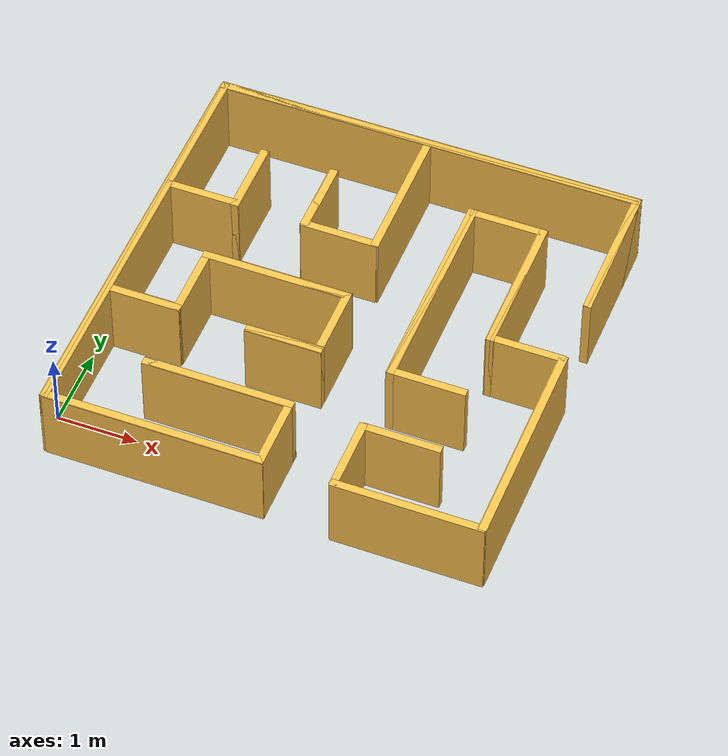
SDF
<sdf version='1.5'>
<model name='maze_test'>
      <link name='Wall_0'>
        <self_collide>0</self_collide>
        <kinematic>0</kinematic>
        <visual name='Wall_0_Visual'>
          <pose>2.5949999999999998 5.28 0 0 0 0</pose>
          <geometry>
            <box>
              <size>5.47 0.1 1</size>
            </box>
          </geometry>
          <material>
            <script>
              <uri>file://media/materials/scripts/gazebo.material</uri>
              <name>Gazebo/Grey</name>
            </script>
            <ambient>1 0.764706 0.305882 1</ambient>
            <diffuse>0.7 0.7 0.7 1</diffuse>
            <specular>0.01 0.01 0.01 1</specular>
            <emissive>0 0 0 1</emissive>
            <shader type='pixel'/>
          </material>
          <cast_shadows>1</cast_shadows>
          <transparency>0</transparency>
        </visual>
        <collision name='Wall_0_Collision'>
          <laser_retro>0</laser_retro>
          <max_contacts>10</max_contacts>
          <pose>2.5949999999999998 5.28 0 0 0 0</pose>
          <geometry>
            <box>
              <size>5.47 0.1 1</size>
            </box>
          </geometry>
          <surface>
            <friction>
              <ode>
                <mu>1</mu>
                <mu2>1</mu2>
                <fdir1>0 0 0</fdir1>
                <slip1>0</slip1>
                <slip2>0</slip2>
              </ode>
              <torsional>
                <ode/>
              </torsional>
            </friction>
            <bounce>
              <restitution_coefficient>0</restitution_coefficient>
              <threshold>1e+06</threshold>
            </bounce>
            <contact>
              <collide_without_contact>0</collide_without_contact>
              <collide_without_contact_bitmask>1</collide_without_contact_bitmask>
              <collide_bitmask>1</collide_bitmask>
              <ode>
                <soft_cfm>0</soft_cfm>
                <soft_erp>0.2</soft_erp>
                <kp>1e+13</kp>
                <kd>1</kd>
                <max_vel>0.01</max_vel>
                <min_depth>0</min_depth>
              </ode>
              <bullet>
                <split_impulse>1</split_impulse>
                <split_impulse_penetration_threshold>-0.01</split_impulse_penetration_threshold>
                <soft_cfm>0</soft_cfm>
                <soft_erp>0.2</soft_erp>
                <kp>1e+13</kp>
                <kd>1</kd>
              </bullet>
            </contact>
          </surface>
        </collision>
        <enable_wind>0</enable_wind>
      </link>
      <link name='Wall_1'>
        <self_collide>0</self_collide>
        <kinematic>0</kinematic>
        <visual name='Wall_1_Visual'>
          <pose>4.390000000000001 -0.1 0 0 0 0</pose>
          <geometry>
            <box>
              <size>1.88 0.1 1</size>
            </box>
          </geometry>
          <material>
            <script>
              <uri>file://media/materials/scripts/gazebo.material</uri>
              <name>Gazebo/Grey</name>
            </script>
            <ambient>1 0.764706 0.305882 1</ambient>
            <diffuse>0.7 0.7 0.7 1</diffuse>
            <specular>0.01 0.01 0.01 1</specular>
            <emissive>0 0 0 1</emissive>
            <shader type='pixel'/>
          </material>
          <cast_shadows>1</cast_shadows>
          <transparency>0</transparency>
        </visual>
        <collision name='Wall_1_Collision'>
          <laser_retro>0</laser_retro>
          <max_contacts>10</max_contacts>
          <pose>4.390000000000001 -0.1 0 0 0 0</pose>
          <geometry>
            <box>
              <size>1.88 0.1 1</size>
            </box>
          </geometry>
          <surface>
            <friction>
              <ode>
                <mu>1</mu>
                <mu2>1</mu2>
                <fdir1>0 0 0</fdir1>
                <slip1>0</slip1>
                <slip2>0</slip2>
              </ode>
              <torsional>
                <ode/>
              </torsional>
            </friction>
            <bounce>
              <restitution_coefficient>0</restitution_coefficient>
              <threshold>1e+06</threshold>
            </bounce>
            <contact>
              <collide_without_contact>0</collide_without_contact>
              <collide_without_contact_bitmask>1</collide_without_contact_bitmask>
              <collide_bitmask>1</collide_bitmask>
              <ode>
                <soft_cfm>0</soft_cfm>
                <soft_erp>0.2</soft_erp>
                <kp>1e+13</kp>
                <kd>1</kd>
                <max_vel>0.01</max_vel>
                <min_depth>0</min_depth>
              </ode>
              <bullet>
                <split_impulse>1</split_impulse>
                <split_impulse_penetration_threshold>-0.01</split_impulse_penetration_threshold>
                <soft_cfm>0</soft_cfm>
                <soft_erp>0.2</soft_erp>
                <kp>1e+13</kp>
                <kd>1</kd>
              </bullet>
            </contact>
          </surface>
        </collision>
        <enable_wind>0</enable_wind>
      </link>
      <link name='Wall_2'>
        <self_collide>0</self_collide>
        <kinematic>0</kinematic>
        <visual name='Wall_2_Visual'>
          <pose>5.29 1.2550000000000001 0 0 0 0</pose>
          <geometry>
            <box>
              <size>0.1 2.7700000000000005 1</size>
            </box>
          </geometry>
          <material>
            <script>
              <uri>file://media/materials/scripts/gazebo.material</uri>
              <name>Gazebo/Grey</name>
            </script>
            <ambient>1 0.764706 0.305882 1</ambient>
            <diffuse>0.7 0.7 0.7 1</diffuse>
            <specular>0.01 0.01 0.01 1</specular>
            <emissive>0 0 0 1</emissive>
            <shader type='pixel'/>
          </material>
          <cast_shadows>1</cast_shadows>
          <transparency>0</transparency>
        </visual>
        <collision name='Wall_2_Collision'>
          <laser_retro>0</laser_retro>
          <max_contacts>10</max_contacts>
          <pose>5.29 1.2550000000000001 0 0 0 0</pose>
          <geometry>
            <box>
              <size>0.1 2.7700000000000005 1</size>
            </box>
          </geometry>
          <surface>
            <friction>
              <ode>
                <mu>1</mu>
                <mu2>1</mu2>
                <fdir1>0 0 0</fdir1>
                <slip1>0</slip1>
                <slip2>0</slip2>
              </ode>
              <torsional>
                <ode/>
              </torsional>
            </friction>
            <bounce>
              <restitution_coefficient>0</restitution_coefficient>
              <threshold>1e+06</threshold>
            </bounce>
            <contact>
              <collide_without_contact>0</collide_without_contact>
              <collide_without_contact_bitmask>1</collide_without_contact_bitmask>
              <collide_bitmask>1</collide_bitmask>
              <ode>
                <soft_cfm>0</soft_cfm>
                <soft_erp>0.2</soft_erp>
                <kp>1e+13</kp>
                <kd>1</kd>
                <max_vel>0.01</max_vel>
                <min_depth>0</min_depth>
              </ode>
              <bullet>
                <split_impulse>1</split_impulse>
                <split_impulse_penetration_threshold>-0.01</split_impulse_penetration_threshold>
                <soft_cfm>0</soft_cfm>
                <soft_erp>0.2</soft_erp>
                <kp>1e+13</kp>
                <kd>1</kd>
              </bullet>
            </contact>
          </surface>
        </collision>
        <enable_wind>0</enable_wind>
      </link>
      <link name='Wall_3'>
        <self_collide>0</self_collide>
        <kinematic>0</kinematic>
        <visual name='Wall_3_Visual'>
          <pose>-0.09000000000000001 2.5949999999999998 0 0 0 0</pose>
          <geometry>
            <box>
              <size>0.1 5.47 1</size>
            </box>
          </geometry>
          <material>
            <script>
              <uri>file://media/materials/scripts/gazebo.material</uri>
              <name>Gazebo/Grey</name>
            </script>
            <ambient>1 0.764706 0.305882 1</ambient>
            <diffuse>0.7 0.7 0.7 1</diffuse>
            <specular>0.01 0.01 0.01 1</specular>
            <emissive>0 0 0 1</emissive>
            <shader type='pixel'/>
          </material>
          <cast_shadows>1</cast_shadows>
          <transparency>0</transparency>
        </visual>
        <collision name='Wall_3_Collision'>
          <laser_retro>0</laser_retro>
          <max_contacts>10</max_contacts>
          <pose>-0.09000000000000001 2.5949999999999998 0 0 0 0</pose>
          <geometry>
            <box>
              <size>0.1 5.47 1</size>
            </box>
          </geometry>
          <surface>
            <friction>
              <ode>
                <mu>1</mu>
                <mu2>1</mu2>
                <fdir1>0 0 0</fdir1>
                <slip1>0</slip1>
                <slip2>0</slip2>
              </ode>
              <torsional>
                <ode/>
              </torsional>
            </friction>
            <bounce>
              <restitution_coefficient>0</restitution_coefficient>
              <threshold>1e+06</threshold>
            </bounce>
            <contact>
              <collide_without_contact>0</collide_without_contact>
              <collide_without_contact_bitmask>1</collide_without_contact_bitmask>
              <collide_bitmask>1</collide_bitmask>
              <ode>
                <soft_cfm>0</soft_cfm>
                <soft_erp>0.2</soft_erp>
                <kp>1e+13</kp>
                <kd>1</kd>
                <max_vel>0.01</max_vel>
                <min_depth>0</min_depth>
              </ode>
              <bullet>
                <split_impulse>1</split_impulse>
                <split_impulse_penetration_threshold>-0.01</split_impulse_penetration_threshold>
                <soft_cfm>0</soft_cfm>
                <soft_erp>0.2</soft_erp>
                <kp>1e+13</kp>
                <kd>1</kd>
              </bullet>
            </contact>
          </surface>
        </collision>
        <enable_wind>0</enable_wind>
      </link>
      <link name='Wall_4'>
        <self_collide>0</self_collide>
        <kinematic>0</kinematic>
        <visual name='Wall_4_Visual'>
          <pose>1.25 -0.09000000000000001 0 0 0 0</pose>
          <geometry>
            <box>
              <size>2.7800000000000002 0.1 1</size>
            </box>
          </geometry>
          <material>
            <script>
              <uri>file://media/materials/scripts/gazebo.material</uri>
              <name>Gazebo/Grey</name>
            </script>
            <ambient>1 0.764706 0.305882 1</ambient>
            <diffuse>0.7 0.7 0.7 1</diffuse>
            <specular>0.01 0.01 0.01 1</specular>
            <emissive>0 0 0 1</emissive>
            <shader type='pixel'/>
          </material>
          <cast_shadows>1</cast_shadows>
          <transparency>0</transparency>
        </visual>
        <collision name='Wall_4_Collision'>
          <laser_retro>0</laser_retro>
          <max_contacts>10</max_contacts>
          <pose>1.25 -0.09000000000000001 0 0 0 0</pose>
          <geometry>
            <box>
              <size>2.7800000000000002 0.1 1</size>
            </box>
          </geometry>
          <surface>
            <friction>
              <ode>
                <mu>1</mu>
                <mu2>1</mu2>
                <fdir1>0 0 0</fdir1>
                <slip1>0</slip1>
                <slip2>0</slip2>
              </ode>
              <torsional>
                <ode/>
              </torsional>
            </friction>
            <bounce>
              <restitution_coefficient>0</restitution_coefficient>
              <threshold>1e+06</threshold>
            </bounce>
            <contact>
              <collide_without_contact>0</collide_without_contact>
              <collide_without_contact_bitmask>1</collide_without_contact_bitmask>
              <collide_bitmask>1</collide_bitmask>
              <ode>
                <soft_cfm>0</soft_cfm>
                <soft_erp>0.2</soft_erp>
                <kp>1e+13</kp>
                <kd>1</kd>
                <max_vel>0.01</max_vel>
                <min_depth>0</min_depth>
              </ode>
              <bullet>
                <split_impulse>1</split_impulse>
                <split_impulse_penetration_threshold>-0.01</split_impulse_penetration_threshold>
                <soft_cfm>0</soft_cfm>
                <soft_erp>0.2</soft_erp>
                <kp>1e+13</kp>
                <kd>1</kd>
              </bullet>
            </contact>
          </surface>
        </collision>
        <enable_wind>0</enable_wind>
      </link>
      <link name='Wall_5'>
        <self_collide>0</self_collide>
        <kinematic>0</kinematic>
        <visual name='Wall_5_Visual'>
          <pose>5.28 4.4 0 0 0 0</pose>
          <geometry>
            <box>
              <size>0.1 1.8599999999999999 1</size>
            </box>
          </geometry>
          <material>
            <script>
              <uri>file://media/materials/scripts/gazebo.material</uri>
              <name>Gazebo/Grey</name>
            </script>
            <ambient>1 0.764706 0.305882 1</ambient>
            <diffuse>0.7 0.7 0.7 1</diffuse>
            <specular>0.01 0.01 0.01 1</specular>
            <emissive>0 0 0 1</emissive>
            <shader type='pixel'/>
          </material>
          <cast_shadows>1</cast_shadows>
          <transparency>0</transparency>
        </visual>
        <collision name='Wall_5_Collision'>
          <laser_retro>0</laser_retro>
          <max_contacts>10</max_contacts>
          <pose>5.28 4.4 0 0 0 0</pose>
          <geometry>
            <box>
              <size>0.1 1.8599999999999999 1</size>
            </box>
          </geometry>
          <surface>
            <friction>
              <ode>
                <mu>1</mu>
                <mu2>1</mu2>
                <fdir1>0 0 0</fdir1>
                <slip1>0</slip1>
                <slip2>0</slip2>
              </ode>
              <torsional>
                <ode/>
              </torsional>
            </friction>
            <bounce>
              <restitution_coefficient>0</restitution_coefficient>
              <threshold>1e+06</threshold>
            </bounce>
            <contact>
              <collide_without_contact>0</collide_without_contact>
              <collide_without_contact_bitmask>1</collide_without_contact_bitmask>
              <collide_bitmask>1</collide_bitmask>
              <ode>
                <soft_cfm>0</soft_cfm>
                <soft_erp>0.2</soft_erp>
                <kp>1e+13</kp>
                <kd>1</kd>
                <max_vel>0.01</max_vel>
                <min_depth>0</min_depth>
              </ode>
              <bullet>
                <split_impulse>1</split_impulse>
                <split_impulse_penetration_threshold>-0.01</split_impulse_penetration_threshold>
                <soft_cfm>0</soft_cfm>
                <soft_erp>0.2</soft_erp>
                <kp>1e+13</kp>
                <kd>1</kd>
              </bullet>
            </contact>
          </surface>
        </collision>
        <enable_wind>0</enable_wind>
      </link>
      <link name='Wall_6'>
        <self_collide>0</self_collide>
        <kinematic>0</kinematic>
        <visual name='Wall_6_Visual'>
          <pose>2.5949999999999998 5.29 0 0 0 0</pose>
          <geometry>
            <box>
              <size>5.47 0.1 1</size>
            </box>
          </geometry>
          <material>
            <script>
              <uri>file://media/materials/scripts/gazebo.material</uri>
              <name>Gazebo/Grey</name>
            </script>
            <ambient>1 0.764706 0.305882 1</ambient>
            <diffuse>0.7 0.7 0.7 1</diffuse>
            <specular>0.01 0.01 0.01 1</specular>
            <emissive>0 0 0 1</emissive>
            <shader type='pixel'/>
          </material>
          <cast_shadows>1</cast_shadows>
          <transparency>0</transparency>
        </visual>
        <collision name='Wall_6_Collision'>
          <laser_retro>0</laser_retro>
          <max_contacts>10</max_contacts>
          <pose>2.5949999999999998 5.29 0 0 0 0</pose>
          <geometry>
            <box>
              <size>5.47 0.1 1</size>
            </box>
          </geometry>
          <surface>
            <friction>
              <ode>
                <mu>1</mu>
                <mu2>1</mu2>
                <fdir1>0 0 0</fdir1>
                <slip1>0</slip1>
                <slip2>0</slip2>
              </ode>
              <torsional>
                <ode/>
              </torsional>
            </friction>
            <bounce>
              <restitution_coefficient>0</restitution_coefficient>
              <threshold>1e+06</threshold>
            </bounce>
            <contact>
              <collide_without_contact>0</collide_without_contact>
              <collide_without_contact_bitmask>1</collide_without_contact_bitmask>
              <collide_bitmask>1</collide_bitmask>
              <ode>
                <soft_cfm>0</soft_cfm>
                <soft_erp>0.2</soft_erp>
                <kp>1e+13</kp>
                <kd>1</kd>
                <max_vel>0.01</max_vel>
                <min_depth>0</min_depth>
              </ode>
              <bullet>
                <split_impulse>1</split_impulse>
                <split_impulse_penetration_threshold>-0.01</split_impulse_penetration_threshold>
                <soft_cfm>0</soft_cfm>
                <soft_erp>0.2</soft_erp>
                <kp>1e+13</kp>
                <kd>1</kd>
              </bullet>
            </contact>
          </surface>
        </collision>
        <enable_wind>0</enable_wind>
      </link>
      <link name='Wall_7'>
        <self_collide>0</self_collide>
        <kinematic>0</kinematic>
        <visual name='Wall_7_Visual'>
          <pose>2.59 2.145 0 0 0 0</pose>
          <geometry>
            <box>
              <size>0.1 0.9900000000000001 1</size>
            </box>
          </geometry>
          <material>
            <script>
              <uri>file://media/materials/scripts/gazebo.material</uri>
              <name>Gazebo/Grey</name>
            </script>
            <ambient>1 0.764706 0.305882 1</ambient>
            <diffuse>0.7 0.7 0.7 1</diffuse>
            <specular>0.01 0.01 0.01 1</specular>
            <emissive>0 0 0 1</emissive>
            <shader type='pixel'/>
          </material>
          <cast_shadows>1</cast_shadows>
          <transparency>0</transparency>
        </visual>
        <collision name='Wall_7_Collision'>
          <laser_retro>0</laser_retro>
          <max_contacts>10</max_contacts>
          <pose>2.59 2.145 0 0 0 0</pose>
          <geometry>
            <box>
              <size>0.1 0.9900000000000001 1</size>
            </box>
          </geometry>
          <surface>
            <friction>
              <ode>
                <mu>1</mu>
                <mu2>1</mu2>
                <fdir1>0 0 0</fdir1>
                <slip1>0</slip1>
                <slip2>0</slip2>
              </ode>
              <torsional>
                <ode/>
              </torsional>
            </friction>
            <bounce>
              <restitution_coefficient>0</restitution_coefficient>
              <threshold>1e+06</threshold>
            </bounce>
            <contact>
              <collide_without_contact>0</collide_without_contact>
              <collide_without_contact_bitmask>1</collide_without_contact_bitmask>
              <collide_bitmask>1</collide_bitmask>
              <ode>
                <soft_cfm>0</soft_cfm>
                <soft_erp>0.2</soft_erp>
                <kp>1e+13</kp>
                <kd>1</kd>
                <max_vel>0.01</max_vel>
                <min_depth>0</min_depth>
              </ode>
              <bullet>
                <split_impulse>1</split_impulse>
                <split_impulse_penetration_threshold>-0.01</split_impulse_penetration_threshold>
                <soft_cfm>0</soft_cfm>
                <soft_erp>0.2</soft_erp>
                <kp>1e+13</kp>
                <kd>1</kd>
              </bullet>
            </contact>
          </surface>
        </collision>
        <enable_wind>0</enable_wind>
      </link>
      <link name='Wall_8'>
        <self_collide>0</self_collide>
        <kinematic>0</kinematic>
        <visual name='Wall_8_Visual'>
          <pose>-0.1 2.585 0 0 0 0</pose>
          <geometry>
            <box>
              <size>0.1 5.45 1</size>
            </box>
          </geometry>
          <material>
            <script>
              <uri>file://media/materials/scripts/gazebo.material</uri>
              <name>Gazebo/Grey</name>
            </script>
            <ambient>1 0.764706 0.305882 1</ambient>
            <diffuse>0.7 0.7 0.7 1</diffuse>
            <specular>0.01 0.01 0.01 1</specular>
            <emissive>0 0 0 1</emissive>
            <shader type='pixel'/>
          </material>
          <cast_shadows>1</cast_shadows>
          <transparency>0</transparency>
        </visual>
        <collision name='Wall_8_Collision'>
          <laser_retro>0</laser_retro>
          <max_contacts>10</max_contacts>
          <pose>-0.1 2.585 0 0 0 0</pose>
          <geometry>
            <box>
              <size>0.1 5.45 1</size>
            </box>
          </geometry>
          <surface>
            <friction>
              <ode>
                <mu>1</mu>
                <mu2>1</mu2>
                <fdir1>0 0 0</fdir1>
                <slip1>0</slip1>
                <slip2>0</slip2>
              </ode>
              <torsional>
                <ode/>
              </torsional>
            </friction>
            <bounce>
              <restitution_coefficient>0</restitution_coefficient>
              <threshold>1e+06</threshold>
            </bounce>
            <contact>
              <collide_without_contact>0</collide_without_contact>
              <collide_without_contact_bitmask>1</collide_without_contact_bitmask>
              <collide_bitmask>1</collide_bitmask>
              <ode>
                <soft_cfm>0</soft_cfm>
                <soft_erp>0.2</soft_erp>
                <kp>1e+13</kp>
                <kd>1</kd>
                <max_vel>0.01</max_vel>
                <min_depth>0</min_depth>
              </ode>
              <bullet>
                <split_impulse>1</split_impulse>
                <split_impulse_penetration_threshold>-0.01</split_impulse_penetration_threshold>
                <soft_cfm>0</soft_cfm>
                <soft_erp>0.2</soft_erp>
                <kp>1e+13</kp>
                <kd>1</kd>
              </bullet>
            </contact>
          </surface>
        </collision>
        <enable_wind>0</enable_wind>
      </link>
      <link name='Wall_9'>
        <self_collide>0</self_collide>
        <kinematic>0</kinematic>
        <visual name='Wall_9_Visual'>
          <pose>3.5 3.045 0 0 0 0</pose>
          <geometry>
            <box>
              <size>0.1 2.79 1</size>
            </box>
          </geometry>
          <material>
            <script>
              <uri>file://media/materials/scripts/gazebo.material</uri>
              <name>Gazebo/Grey</name>
            </script>
            <ambient>1 0.764706 0.305882 1</ambient>
            <diffuse>0.7 0.7 0.7 1</diffuse>
            <specular>0.01 0.01 0.01 1</specular>
            <emissive>0 0 0 1</emissive>
            <shader type='pixel'/>
          </material>
          <cast_shadows>1</cast_shadows>
          <transparency>0</transparency>
        </visual>
        <collision name='Wall_9_Collision'>
          <laser_retro>0</laser_retro>
          <max_contacts>10</max_contacts>
          <pose>3.5 3.045 0 0 0 0</pose>
          <geometry>
            <box>
              <size>0.1 2.79 1</size>
            </box>
          </geometry>
          <surface>
            <friction>
              <ode>
                <mu>1</mu>
                <mu2>1</mu2>
                <fdir1>0 0 0</fdir1>
                <slip1>0</slip1>
                <slip2>0</slip2>
              </ode>
              <torsional>
                <ode/>
              </torsional>
            </friction>
            <bounce>
              <restitution_coefficient>0</restitution_coefficient>
              <threshold>1e+06</threshold>
            </bounce>
            <contact>
              <collide_without_contact>0</collide_without_contact>
              <collide_without_contact_bitmask>1</collide_without_contact_bitmask>
              <collide_bitmask>1</collide_bitmask>
              <ode>
                <soft_cfm>0</soft_cfm>
                <soft_erp>0.2</soft_erp>
                <kp>1e+13</kp>
                <kd>1</kd>
                <max_vel>0.01</max_vel>
                <min_depth>0</min_depth>
              </ode>
              <bullet>
                <split_impulse>1</split_impulse>
                <split_impulse_penetration_threshold>-0.01</split_impulse_penetration_threshold>
                <soft_cfm>0</soft_cfm>
                <soft_erp>0.2</soft_erp>
                <kp>1e+13</kp>
                <kd>1</kd>
              </bullet>
            </contact>
          </surface>
        </collision>
        <enable_wind>0</enable_wind>
      </link>
      <link name='Wall_10'>
        <self_collide>0</self_collide>
        <kinematic>0</kinematic>
        <visual name='Wall_10_Visual'>
          <pose>2.6 4.380000000000001 0 0 0 0</pose>
          <geometry>
            <box>
              <size>0.1 1.8600000000000003 1</size>
            </box>
          </geometry>
          <material>
            <script>
              <uri>file://media/materials/scripts/gazebo.material</uri>
              <name>Gazebo/Grey</name>
            </script>
            <ambient>1 0.764706 0.305882 1</ambient>
            <diffuse>0.7 0.7 0.7 1</diffuse>
            <specular>0.01 0.01 0.01 1</specular>
            <emissive>0 0 0 1</emissive>
            <shader type='pixel'/>
          </material>
          <cast_shadows>1</cast_shadows>
          <transparency>0</transparency>
        </visual>
        <collision name='Wall_10_Collision'>
          <laser_retro>0</laser_retro>
          <max_contacts>10</max_contacts>
          <pose>2.6 4.380000000000001 0 0 0 0</pose>
          <geometry>
            <box>
              <size>0.1 1.8600000000000003 1</size>
            </box>
          </geometry>
          <surface>
            <friction>
              <ode>
                <mu>1</mu>
                <mu2>1</mu2>
                <fdir1>0 0 0</fdir1>
                <slip1>0</slip1>
                <slip2>0</slip2>
              </ode>
              <torsional>
                <ode/>
              </torsional>
            </friction>
            <bounce>
              <restitution_coefficient>0</restitution_coefficient>
              <threshold>1e+06</threshold>
            </bounce>
            <contact>
              <collide_without_contact>0</collide_without_contact>
              <collide_without_contact_bitmask>1</collide_without_contact_bitmask>
              <collide_bitmask>1</collide_bitmask>
              <ode>
                <soft_cfm>0</soft_cfm>
                <soft_erp>0.2</soft_erp>
                <kp>1e+13</kp>
                <kd>1</kd>
                <max_vel>0.01</max_vel>
                <min_depth>0</min_depth>
              </ode>
              <bullet>
                <split_impulse>1</split_impulse>
                <split_impulse_penetration_threshold>-0.01</split_impulse_penetration_threshold>
                <soft_cfm>0</soft_cfm>
                <soft_erp>0.2</soft_erp>
                <kp>1e+13</kp>
                <kd>1</kd>
              </bullet>
            </contact>
          </surface>
        </collision>
        <enable_wind>0</enable_wind>
      </link>
      <link name='Wall_11'>
        <self_collide>0</self_collide>
        <kinematic>0</kinematic>
        <visual name='Wall_11_Visual'>
          <pose>3.4899999999999998 0.355 0 0 0 0</pose>
          <geometry>
            <box>
              <size>0.1 0.97 1</size>
            </box>
          </geometry>
          <material>
            <script>
              <uri>file://media/materials/scripts/gazebo.material</uri>
              <name>Gazebo/Grey</name>
            </script>
            <ambient>1 0.764706 0.305882 1</ambient>
            <diffuse>0.7 0.7 0.7 1</diffuse>
            <specular>0.01 0.01 0.01 1</specular>
            <emissive>0 0 0 1</emissive>
            <shader type='pixel'/>
          </material>
          <cast_shadows>1</cast_shadows>
          <transparency>0</transparency>
        </visual>
        <collision name='Wall_11_Collision'>
          <laser_retro>0</laser_retro>
          <max_contacts>10</max_contacts>
          <pose>3.4899999999999998 0.355 0 0 0 0</pose>
          <geometry>
            <box>
              <size>0.1 0.97 1</size>
            </box>
          </geometry>
          <surface>
            <friction>
              <ode>
                <mu>1</mu>
                <mu2>1</mu2>
                <fdir1>0 0 0</fdir1>
                <slip1>0</slip1>
                <slip2>0</slip2>
              </ode>
              <torsional>
                <ode/>
              </torsional>
            </friction>
            <bounce>
              <restitution_coefficient>0</restitution_coefficient>
              <threshold>1e+06</threshold>
            </bounce>
            <contact>
              <collide_without_contact>0</collide_without_contact>
              <collide_without_contact_bitmask>1</collide_without_contact_bitmask>
              <collide_bitmask>1</collide_bitmask>
              <ode>
                <soft_cfm>0</soft_cfm>
                <soft_erp>0.2</soft_erp>
                <kp>1e+13</kp>
                <kd>1</kd>
                <max_vel>0.01</max_vel>
                <min_depth>0</min_depth>
              </ode>
              <bullet>
                <split_impulse>1</split_impulse>
                <split_impulse_penetration_threshold>-0.01</split_impulse_penetration_threshold>
                <soft_cfm>0</soft_cfm>
                <soft_erp>0.2</soft_erp>
                <kp>1e+13</kp>
                <kd>1</kd>
              </bullet>
            </contact>
          </surface>
        </collision>
        <enable_wind>0</enable_wind>
      </link>
      <link name='Wall_12'>
        <self_collide>0</self_collide>
        <kinematic>0</kinematic>
        <visual name='Wall_12_Visual'>
          <pose>1.6949999999999998 0.8 0 0 0 0</pose>
          <geometry>
            <box>
              <size>1.8900000000000001 0.1 1</size>
            </box>
          </geometry>
          <material>
            <script>
              <uri>file://media/materials/scripts/gazebo.material</uri>
              <name>Gazebo/Grey</name>
            </script>
            <ambient>1 0.764706 0.305882 1</ambient>
            <diffuse>0.7 0.7 0.7 1</diffuse>
            <specular>0.01 0.01 0.01 1</specular>
            <emissive>0 0 0 1</emissive>
            <shader type='pixel'/>
          </material>
          <cast_shadows>1</cast_shadows>
          <transparency>0</transparency>
        </visual>
        <collision name='Wall_12_Collision'>
          <laser_retro>0</laser_retro>
          <max_contacts>10</max_contacts>
          <pose>1.6949999999999998 0.8 0 0 0 0</pose>
          <geometry>
            <box>
              <size>1.8900000000000001 0.1 1</size>
            </box>
          </geometry>
          <surface>
            <friction>
              <ode>
                <mu>1</mu>
                <mu2>1</mu2>
                <fdir1>0 0 0</fdir1>
                <slip1>0</slip1>
                <slip2>0</slip2>
              </ode>
              <torsional>
                <ode/>
              </torsional>
            </friction>
            <bounce>
              <restitution_coefficient>0</restitution_coefficient>
              <threshold>1e+06</threshold>
            </bounce>
            <contact>
              <collide_without_contact>0</collide_without_contact>
              <collide_without_contact_bitmask>1</collide_without_contact_bitmask>
              <collide_bitmask>1</collide_bitmask>
              <ode>
                <soft_cfm>0</soft_cfm>
                <soft_erp>0.2</soft_erp>
                <kp>1e+13</kp>
                <kd>1</kd>
                <max_vel>0.01</max_vel>
                <min_depth>0</min_depth>
              </ode>
              <bullet>
                <split_impulse>1</split_impulse>
                <split_impulse_penetration_threshold>-0.01</split_impulse_penetration_threshold>
                <soft_cfm>0</soft_cfm>
                <soft_erp>0.2</soft_erp>
                <kp>1e+13</kp>
                <kd>1</kd>
              </bullet>
            </contact>
          </surface>
        </collision>
        <enable_wind>0</enable_wind>
      </link>
      <link name='Wall_13'>
        <self_collide>0</self_collide>
        <kinematic>0</kinematic>
        <visual name='Wall_13_Visual'>
          <pose>1.6949999999999998 0.79 0 0 0 0</pose>
          <geometry>
            <box>
              <size>1.8900000000000001 0.1 1</size>
            </box>
          </geometry>
          <material>
            <script>
              <uri>file://media/materials/scripts/gazebo.material</uri>
              <name>Gazebo/Grey</name>
            </script>
            <ambient>1 0.764706 0.305882 1</ambient>
            <diffuse>0.7 0.7 0.7 1</diffuse>
            <specular>0.01 0.01 0.01 1</specular>
            <emissive>0 0 0 1</emissive>
            <shader type='pixel'/>
          </material>
          <cast_shadows>1</cast_shadows>
          <transparency>0</transparency>
        </visual>
        <collision name='Wall_13_Collision'>
          <laser_retro>0</laser_retro>
          <max_contacts>10</max_contacts>
          <pose>1.6949999999999998 0.79 0 0 0 0</pose>
          <geometry>
            <box>
              <size>1.8900000000000001 0.1 1</size>
            </box>
          </geometry>
          <surface>
            <friction>
              <ode>
                <mu>1</mu>
                <mu2>1</mu2>
                <fdir1>0 0 0</fdir1>
                <slip1>0</slip1>
                <slip2>0</slip2>
              </ode>
              <torsional>
                <ode/>
              </torsional>
            </friction>
            <bounce>
              <restitution_coefficient>0</restitution_coefficient>
              <threshold>1e+06</threshold>
            </bounce>
            <contact>
              <collide_without_contact>0</collide_without_contact>
              <collide_without_contact_bitmask>1</collide_without_contact_bitmask>
              <collide_bitmask>1</collide_bitmask>
              <ode>
                <soft_cfm>0</soft_cfm>
                <soft_erp>0.2</soft_erp>
                <kp>1e+13</kp>
                <kd>1</kd>
                <max_vel>0.01</max_vel>
                <min_depth>0</min_depth>
              </ode>
              <bullet>
                <split_impulse>1</split_impulse>
                <split_impulse_penetration_threshold>-0.01</split_impulse_penetration_threshold>
                <soft_cfm>0</soft_cfm>
                <soft_erp>0.2</soft_erp>
                <kp>1e+13</kp>
                <kd>1</kd>
              </bullet>
            </contact>
          </surface>
        </collision>
        <enable_wind>0</enable_wind>
      </link>
      <link name='Wall_14'>
        <self_collide>0</self_collide>
        <kinematic>0</kinematic>
        <visual name='Wall_14_Visual'>
          <pose>1.6949999999999998 2.59 0 0 0 0</pose>
          <geometry>
            <box>
              <size>1.8900000000000001 0.1 1</size>
            </box>
          </geometry>
          <material>
            <script>
              <uri>file://media/materials/scripts/gazebo.material</uri>
              <name>Gazebo/Grey</name>
            </script>
            <ambient>1 0.764706 0.305882 1</ambient>
            <diffuse>0.7 0.7 0.7 1</diffuse>
            <specular>0.01 0.01 0.01 1</specular>
            <emissive>0 0 0 1</emissive>
            <shader type='pixel'/>
          </material>
          <cast_shadows>1</cast_shadows>
          <transparency>0</transparency>
        </visual>
        <collision name='Wall_14_Collision'>
          <laser_retro>0</laser_retro>
          <max_contacts>10</max_contacts>
          <pose>1.6949999999999998 2.59 0 0 0 0</pose>
          <geometry>
            <box>
              <size>1.8900000000000001 0.1 1</size>
            </box>
          </geometry>
          <surface>
            <friction>
              <ode>
                <mu>1</mu>
                <mu2>1</mu2>
                <fdir1>0 0 0</fdir1>
                <slip1>0</slip1>
                <slip2>0</slip2>
              </ode>
              <torsional>
                <ode/>
              </torsional>
            </friction>
            <bounce>
              <restitution_coefficient>0</restitution_coefficient>
              <threshold>1e+06</threshold>
            </bounce>
            <contact>
              <collide_without_contact>0</collide_without_contact>
              <collide_without_contact_bitmask>1</collide_without_contact_bitmask>
              <collide_bitmask>1</collide_bitmask>
              <ode>
                <soft_cfm>0</soft_cfm>
                <soft_erp>0.2</soft_erp>
                <kp>1e+13</kp>
                <kd>1</kd>
                <max_vel>0.01</max_vel>
                <min_depth>0</min_depth>
              </ode>
              <bullet>
                <split_impulse>1</split_impulse>
                <split_impulse_penetration_threshold>-0.01</split_impulse_penetration_threshold>
                <soft_cfm>0</soft_cfm>
                <soft_erp>0.2</soft_erp>
                <kp>1e+13</kp>
                <kd>1</kd>
              </bullet>
            </contact>
          </surface>
        </collision>
        <enable_wind>0</enable_wind>
      </link>
      <link name='Wall_15'>
        <self_collide>0</self_collide>
        <kinematic>0</kinematic>
        <visual name='Wall_15_Visual'>
          <pose>1.6949999999999998 2.6 0 0 0 0</pose>
          <geometry>
            <box>
              <size>1.8900000000000001 0.1 1</size>
            </box>
          </geometry>
          <material>
            <script>
              <uri>file://media/materials/scripts/gazebo.material</uri>
              <name>Gazebo/Grey</name>
            </script>
            <ambient>1 0.764706 0.305882 1</ambient>
            <diffuse>0.7 0.7 0.7 1</diffuse>
            <specular>0.01 0.01 0.01 1</specular>
            <emissive>0 0 0 1</emissive>
            <shader type='pixel'/>
          </material>
          <cast_shadows>1</cast_shadows>
          <transparency>0</transparency>
        </visual>
        <collision name='Wall_15_Collision'>
          <laser_retro>0</laser_retro>
          <max_contacts>10</max_contacts>
          <pose>1.6949999999999998 2.6 0 0 0 0</pose>
          <geometry>
            <box>
              <size>1.8900000000000001 0.1 1</size>
            </box>
          </geometry>
          <surface>
            <friction>
              <ode>
                <mu>1</mu>
                <mu2>1</mu2>
                <fdir1>0 0 0</fdir1>
                <slip1>0</slip1>
                <slip2>0</slip2>
              </ode>
              <torsional>
                <ode/>
              </torsional>
            </friction>
            <bounce>
              <restitution_coefficient>0</restitution_coefficient>
              <threshold>1e+06</threshold>
            </bounce>
            <contact>
              <collide_without_contact>0</collide_without_contact>
              <collide_without_contact_bitmask>1</collide_without_contact_bitmask>
              <collide_bitmask>1</collide_bitmask>
              <ode>
                <soft_cfm>0</soft_cfm>
                <soft_erp>0.2</soft_erp>
                <kp>1e+13</kp>
                <kd>1</kd>
                <max_vel>0.01</max_vel>
                <min_depth>0</min_depth>
              </ode>
              <bullet>
                <split_impulse>1</split_impulse>
                <split_impulse_penetration_threshold>-0.01</split_impulse_penetration_threshold>
                <soft_cfm>0</soft_cfm>
                <soft_erp>0.2</soft_erp>
                <kp>1e+13</kp>
                <kd>1</kd>
              </bullet>
            </contact>
          </surface>
        </collision>
        <enable_wind>0</enable_wind>
      </link>
      <link name='Wall_16'>
        <self_collide>0</self_collide>
        <kinematic>0</kinematic>
        <visual name='Wall_16_Visual'>
          <pose>2.155 1.7 0 0 0 0</pose>
          <geometry>
            <box>
              <size>0.9700000000000001 0.1 1</size>
            </box>
          </geometry>
          <material>
            <script>
              <uri>file://media/materials/scripts/gazebo.material</uri>
              <name>Gazebo/Grey</name>
            </script>
            <ambient>1 0.764706 0.305882 1</ambient>
            <diffuse>0.7 0.7 0.7 1</diffuse>
            <specular>0.01 0.01 0.01 1</specular>
            <emissive>0 0 0 1</emissive>
            <shader type='pixel'/>
          </material>
          <cast_shadows>1</cast_shadows>
          <transparency>0</transparency>
        </visual>
        <collision name='Wall_16_Collision'>
          <laser_retro>0</laser_retro>
          <max_contacts>10</max_contacts>
          <pose>2.155 1.7 0 0 0 0</pose>
          <geometry>
            <box>
              <size>0.9700000000000001 0.1 1</size>
            </box>
          </geometry>
          <surface>
            <friction>
              <ode>
                <mu>1</mu>
                <mu2>1</mu2>
                <fdir1>0 0 0</fdir1>
                <slip1>0</slip1>
                <slip2>0</slip2>
              </ode>
              <torsional>
                <ode/>
              </torsional>
            </friction>
            <bounce>
              <restitution_coefficient>0</restitution_coefficient>
              <threshold>1e+06</threshold>
            </bounce>
            <contact>
              <collide_without_contact>0</collide_without_contact>
              <collide_without_contact_bitmask>1</collide_without_contact_bitmask>
              <collide_bitmask>1</collide_bitmask>
              <ode>
                <soft_cfm>0</soft_cfm>
                <soft_erp>0.2</soft_erp>
                <kp>1e+13</kp>
                <kd>1</kd>
                <max_vel>0.01</max_vel>
                <min_depth>0</min_depth>
              </ode>
              <bullet>
                <split_impulse>1</split_impulse>
                <split_impulse_penetration_threshold>-0.01</split_impulse_penetration_threshold>
                <soft_cfm>0</soft_cfm>
                <soft_erp>0.2</soft_erp>
                <kp>1e+13</kp>
                <kd>1</kd>
              </bullet>
            </contact>
          </surface>
        </collision>
        <enable_wind>0</enable_wind>
      </link>
      <link name='Wall_17'>
        <self_collide>0</self_collide>
        <kinematic>0</kinematic>
        <visual name='Wall_17_Visual'>
          <pose>2.155 1.69 0 0 0 0</pose>
          <geometry>
            <box>
              <size>0.9700000000000001 0.1 1</size>
            </box>
          </geometry>
          <material>
            <script>
              <uri>file://media/materials/scripts/gazebo.material</uri>
              <name>Gazebo/Grey</name>
            </script>
            <ambient>1 0.764706 0.305882 1</ambient>
            <diffuse>0.7 0.7 0.7 1</diffuse>
            <specular>0.01 0.01 0.01 1</specular>
            <emissive>0 0 0 1</emissive>
            <shader type='pixel'/>
          </material>
          <cast_shadows>1</cast_shadows>
          <transparency>0</transparency>
        </visual>
        <collision name='Wall_17_Collision'>
          <laser_retro>0</laser_retro>
          <max_contacts>10</max_contacts>
          <pose>2.155 1.69 0 0 0 0</pose>
          <geometry>
            <box>
              <size>0.9700000000000001 0.1 1</size>
            </box>
          </geometry>
          <surface>
            <friction>
              <ode>
                <mu>1</mu>
                <mu2>1</mu2>
                <fdir1>0 0 0</fdir1>
                <slip1>0</slip1>
                <slip2>0</slip2>
              </ode>
              <torsional>
                <ode/>
              </torsional>
            </friction>
            <bounce>
              <restitution_coefficient>0</restitution_coefficient>
              <threshold>1e+06</threshold>
            </bounce>
            <contact>
              <collide_without_contact>0</collide_without_contact>
              <collide_without_contact_bitmask>1</collide_without_contact_bitmask>
              <collide_bitmask>1</collide_bitmask>
              <ode>
                <soft_cfm>0</soft_cfm>
                <soft_erp>0.2</soft_erp>
                <kp>1e+13</kp>
                <kd>1</kd>
                <max_vel>0.01</max_vel>
                <min_depth>0</min_depth>
              </ode>
              <bullet>
                <split_impulse>1</split_impulse>
                <split_impulse_penetration_threshold>-0.01</split_impulse_penetration_threshold>
                <soft_cfm>0</soft_cfm>
                <soft_erp>0.2</soft_erp>
                <kp>1e+13</kp>
                <kd>1</kd>
              </bullet>
            </contact>
          </surface>
        </collision>
        <enable_wind>0</enable_wind>
      </link>
      <link name='Wall_18'>
        <self_collide>0</self_collide>
        <kinematic>0</kinematic>
        <visual name='Wall_18_Visual'>
          <pose>4.390000000000001 3.4949999999999997 0 0 0 0</pose>
          <geometry>
            <box>
              <size>0.1 1.8900000000000001 1</size>
            </box>
          </geometry>
          <material>
            <script>
              <uri>file://media/materials/scripts/gazebo.material</uri>
              <name>Gazebo/Grey</name>
            </script>
            <ambient>1 0.764706 0.305882 1</ambient>
            <diffuse>0.7 0.7 0.7 1</diffuse>
            <specular>0.01 0.01 0.01 1</specular>
            <emissive>0 0 0 1</emissive>
            <shader type='pixel'/>
          </material>
          <cast_shadows>1</cast_shadows>
          <transparency>0</transparency>
        </visual>
        <collision name='Wall_18_Collision'>
          <laser_retro>0</laser_retro>
          <max_contacts>10</max_contacts>
          <pose>4.390000000000001 3.4949999999999997 0 0 0 0</pose>
          <geometry>
            <box>
              <size>0.1 1.8900000000000001 1</size>
            </box>
          </geometry>
          <surface>
            <friction>
              <ode>
                <mu>1</mu>
                <mu2>1</mu2>
                <fdir1>0 0 0</fdir1>
                <slip1>0</slip1>
                <slip2>0</slip2>
              </ode>
              <torsional>
                <ode/>
              </torsional>
            </friction>
            <bounce>
              <restitution_coefficient>0</restitution_coefficient>
              <threshold>1e+06</threshold>
            </bounce>
            <contact>
              <collide_without_contact>0</collide_without_contact>
              <collide_without_contact_bitmask>1</collide_without_contact_bitmask>
              <collide_bitmask>1</collide_bitmask>
              <ode>
                <soft_cfm>0</soft_cfm>
                <soft_erp>0.2</soft_erp>
                <kp>1e+13</kp>
                <kd>1</kd>
                <max_vel>0.01</max_vel>
                <min_depth>0</min_depth>
              </ode>
              <bullet>
                <split_impulse>1</split_impulse>
                <split_impulse_penetration_threshold>-0.01</split_impulse_penetration_threshold>
                <soft_cfm>0</soft_cfm>
                <soft_erp>0.2</soft_erp>
                <kp>1e+13</kp>
                <kd>1</kd>
              </bullet>
            </contact>
          </surface>
        </collision>
        <enable_wind>0</enable_wind>
      </link>
      <link name='Wall_19'>
        <self_collide>0</self_collide>
        <kinematic>0</kinematic>
        <visual name='Wall_19_Visual'>
          <pose>0.8 3.945 0 0 0 0</pose>
          <geometry>
            <box>
              <size>0.1 0.9900000000000001 1</size>
            </box>
          </geometry>
          <material>
            <script>
              <uri>file://media/materials/scripts/gazebo.material</uri>
              <name>Gazebo/Grey</name>
            </script>
            <ambient>1 0.764706 0.305882 1</ambient>
            <diffuse>0.7 0.7 0.7 1</diffuse>
            <specular>0.01 0.01 0.01 1</specular>
            <emissive>0 0 0 1</emissive>
            <shader type='pixel'/>
          </material>
          <cast_shadows>1</cast_shadows>
          <transparency>0</transparency>
        </visual>
        <collision name='Wall_19_Collision'>
          <laser_retro>0</laser_retro>
          <max_contacts>10</max_contacts>
          <pose>0.8 3.945 0 0 0 0</pose>
          <geometry>
            <box>
              <size>0.1 0.9900000000000001 1</size>
            </box>
          </geometry>
          <surface>
            <friction>
              <ode>
                <mu>1</mu>
                <mu2>1</mu2>
                <fdir1>0 0 0</fdir1>
                <slip1>0</slip1>
                <slip2>0</slip2>
              </ode>
              <torsional>
                <ode/>
              </torsional>
            </friction>
            <bounce>
              <restitution_coefficient>0</restitution_coefficient>
              <threshold>1e+06</threshold>
            </bounce>
            <contact>
              <collide_without_contact>0</collide_without_contact>
              <collide_without_contact_bitmask>1</collide_without_contact_bitmask>
              <collide_bitmask>1</collide_bitmask>
              <ode>
                <soft_cfm>0</soft_cfm>
                <soft_erp>0.2</soft_erp>
                <kp>1e+13</kp>
                <kd>1</kd>
                <max_vel>0.01</max_vel>
                <min_depth>0</min_depth>
              </ode>
              <bullet>
                <split_impulse>1</split_impulse>
                <split_impulse_penetration_threshold>-0.01</split_impulse_penetration_threshold>
                <soft_cfm>0</soft_cfm>
                <soft_erp>0.2</soft_erp>
                <kp>1e+13</kp>
                <kd>1</kd>
              </bullet>
            </contact>
          </surface>
        </collision>
        <enable_wind>0</enable_wind>
      </link>
      <link name='Wall_20'>
        <self_collide>0</self_collide>
        <kinematic>0</kinematic>
        <visual name='Wall_20_Visual'>
          <pose>4.4 3.4949999999999997 0 0 0 0</pose>
          <geometry>
            <box>
              <size>0.1 1.8900000000000001 1</size>
            </box>
          </geometry>
          <material>
            <script>
              <uri>file://media/materials/scripts/gazebo.material</uri>
              <name>Gazebo/Grey</name>
            </script>
            <ambient>1 0.764706 0.305882 1</ambient>
            <diffuse>0.7 0.7 0.7 1</diffuse>
            <specular>0.01 0.01 0.01 1</specular>
            <emissive>0 0 0 1</emissive>
            <shader type='pixel'/>
          </material>
          <cast_shadows>1</cast_shadows>
          <transparency>0</transparency>
        </visual>
        <collision name='Wall_20_Collision'>
          <laser_retro>0</laser_retro>
          <max_contacts>10</max_contacts>
          <pose>4.4 3.4949999999999997 0 0 0 0</pose>
          <geometry>
            <box>
              <size>0.1 1.8900000000000001 1</size>
            </box>
          </geometry>
          <surface>
            <friction>
              <ode>
                <mu>1</mu>
                <mu2>1</mu2>
                <fdir1>0 0 0</fdir1>
                <slip1>0</slip1>
                <slip2>0</slip2>
              </ode>
              <torsional>
                <ode/>
              </torsional>
            </friction>
            <bounce>
              <restitution_coefficient>0</restitution_coefficient>
              <threshold>1e+06</threshold>
            </bounce>
            <contact>
              <collide_without_contact>0</collide_without_contact>
              <collide_without_contact_bitmask>1</collide_without_contact_bitmask>
              <collide_bitmask>1</collide_bitmask>
              <ode>
                <soft_cfm>0</soft_cfm>
                <soft_erp>0.2</soft_erp>
                <kp>1e+13</kp>
                <kd>1</kd>
                <max_vel>0.01</max_vel>
                <min_depth>0</min_depth>
              </ode>
              <bullet>
                <split_impulse>1</split_impulse>
                <split_impulse_penetration_threshold>-0.01</split_impulse_penetration_threshold>
                <soft_cfm>0</soft_cfm>
                <soft_erp>0.2</soft_erp>
                <kp>1e+13</kp>
                <kd>1</kd>
              </bullet>
            </contact>
          </surface>
        </collision>
        <enable_wind>0</enable_wind>
      </link>
      <link name='Wall_21'>
        <self_collide>0</self_collide>
        <kinematic>0</kinematic>
        <visual name='Wall_21_Visual'>
          <pose>2.14 3.4899999999999998 0 0 0 0</pose>
          <geometry>
            <box>
              <size>0.9799999999999999 0.1 1</size>
            </box>
          </geometry>
          <material>
            <script>
              <uri>file://media/materials/scripts/gazebo.material</uri>
              <name>Gazebo/Grey</name>
            </script>
            <ambient>1 0.764706 0.305882 1</ambient>
            <diffuse>0.7 0.7 0.7 1</diffuse>
            <specular>0.01 0.01 0.01 1</specular>
            <emissive>0 0 0 1</emissive>
            <shader type='pixel'/>
          </material>
          <cast_shadows>1</cast_shadows>
          <transparency>0</transparency>
        </visual>
        <collision name='Wall_21_Collision'>
          <laser_retro>0</laser_retro>
          <max_contacts>10</max_contacts>
          <pose>2.14 3.4899999999999998 0 0 0 0</pose>
          <geometry>
            <box>
              <size>0.9799999999999999 0.1 1</size>
            </box>
          </geometry>
          <surface>
            <friction>
              <ode>
                <mu>1</mu>
                <mu2>1</mu2>
                <fdir1>0 0 0</fdir1>
                <slip1>0</slip1>
                <slip2>0</slip2>
              </ode>
              <torsional>
                <ode/>
              </torsional>
            </friction>
            <bounce>
              <restitution_coefficient>0</restitution_coefficient>
              <threshold>1e+06</threshold>
            </bounce>
            <contact>
              <collide_without_contact>0</collide_without_contact>
              <collide_without_contact_bitmask>1</collide_without_contact_bitmask>
              <collide_bitmask>1</collide_bitmask>
              <ode>
                <soft_cfm>0</soft_cfm>
                <soft_erp>0.2</soft_erp>
                <kp>1e+13</kp>
                <kd>1</kd>
                <max_vel>0.01</max_vel>
                <min_depth>0</min_depth>
              </ode>
              <bullet>
                <split_impulse>1</split_impulse>
                <split_impulse_penetration_threshold>-0.01</split_impulse_penetration_threshold>
                <soft_cfm>0</soft_cfm>
                <soft_erp>0.2</soft_erp>
                <kp>1e+13</kp>
                <kd>1</kd>
              </bullet>
            </contact>
          </surface>
        </collision>
        <enable_wind>0</enable_wind>
      </link>
      <link name='Wall_22'>
        <self_collide>0</self_collide>
        <kinematic>0</kinematic>
        <visual name='Wall_22_Visual'>
          <pose>0.79 3.945 0 0 0 0</pose>
          <geometry>
            <box>
              <size>0.1 0.9900000000000001 1</size>
            </box>
          </geometry>
          <material>
            <script>
              <uri>file://media/materials/scripts/gazebo.material</uri>
              <name>Gazebo/Grey</name>
            </script>
            <ambient>1 0.764706 0.305882 1</ambient>
            <diffuse>0.7 0.7 0.7 1</diffuse>
            <specular>0.01 0.01 0.01 1</specular>
            <emissive>0 0 0 1</emissive>
            <shader type='pixel'/>
          </material>
          <cast_shadows>1</cast_shadows>
          <transparency>0</transparency>
        </visual>
        <collision name='Wall_22_Collision'>
          <laser_retro>0</laser_retro>
          <max_contacts>10</max_contacts>
          <pose>0.79 3.945 0 0 0 0</pose>
          <geometry>
            <box>
              <size>0.1 0.9900000000000001 1</size>
            </box>
          </geometry>
          <surface>
            <friction>
              <ode>
                <mu>1</mu>
                <mu2>1</mu2>
                <fdir1>0 0 0</fdir1>
                <slip1>0</slip1>
                <slip2>0</slip2>
              </ode>
              <torsional>
                <ode/>
              </torsional>
            </friction>
            <bounce>
              <restitution_coefficient>0</restitution_coefficient>
              <threshold>1e+06</threshold>
            </bounce>
            <contact>
              <collide_without_contact>0</collide_without_contact>
              <collide_without_contact_bitmask>1</collide_without_contact_bitmask>
              <collide_bitmask>1</collide_bitmask>
              <ode>
                <soft_cfm>0</soft_cfm>
                <soft_erp>0.2</soft_erp>
                <kp>1e+13</kp>
                <kd>1</kd>
                <max_vel>0.01</max_vel>
                <min_depth>0</min_depth>
              </ode>
              <bullet>
                <split_impulse>1</split_impulse>
                <split_impulse_penetration_threshold>-0.01</split_impulse_penetration_threshold>
                <soft_cfm>0</soft_cfm>
                <soft_erp>0.2</soft_erp>
                <kp>1e+13</kp>
                <kd>1</kd>
              </bullet>
            </contact>
          </surface>
        </collision>
        <enable_wind>0</enable_wind>
      </link>
      <link name='Wall_23'>
        <self_collide>0</self_collide>
        <kinematic>0</kinematic>
        <visual name='Wall_23_Visual'>
          <pose>0.35 3.5 0 0 0 0</pose>
          <geometry>
            <box>
              <size>0.94 0.1 1</size>
            </box>
          </geometry>
          <material>
            <script>
              <uri>file://media/materials/scripts/gazebo.material</uri>
              <name>Gazebo/Grey</name>
            </script>
            <ambient>1 0.764706 0.305882 1</ambient>
            <diffuse>0.7 0.7 0.7 1</diffuse>
            <specular>0.01 0.01 0.01 1</specular>
            <emissive>0 0 0 1</emissive>
            <shader type='pixel'/>
          </material>
          <cast_shadows>1</cast_shadows>
          <transparency>0</transparency>
        </visual>
        <collision name='Wall_23_Collision'>
          <laser_retro>0</laser_retro>
          <max_contacts>10</max_contacts>
          <pose>0.35 3.5 0 0 0 0</pose>
          <geometry>
            <box>
              <size>0.94 0.1 1</size>
            </box>
          </geometry>
          <surface>
            <friction>
              <ode>
                <mu>1</mu>
                <mu2>1</mu2>
                <fdir1>0 0 0</fdir1>
                <slip1>0</slip1>
                <slip2>0</slip2>
              </ode>
              <torsional>
                <ode/>
              </torsional>
            </friction>
            <bounce>
              <restitution_coefficient>0</restitution_coefficient>
              <threshold>1e+06</threshold>
            </bounce>
            <contact>
              <collide_without_contact>0</collide_without_contact>
              <collide_without_contact_bitmask>1</collide_without_contact_bitmask>
              <collide_bitmask>1</collide_bitmask>
              <ode>
                <soft_cfm>0</soft_cfm>
                <soft_erp>0.2</soft_erp>
                <kp>1e+13</kp>
                <kd>1</kd>
                <max_vel>0.01</max_vel>
                <min_depth>0</min_depth>
              </ode>
              <bullet>
                <split_impulse>1</split_impulse>
                <split_impulse_penetration_threshold>-0.01</split_impulse_penetration_threshold>
                <soft_cfm>0</soft_cfm>
                <soft_erp>0.2</soft_erp>
                <kp>1e+13</kp>
                <kd>1</kd>
              </bullet>
            </contact>
          </surface>
        </collision>
        <enable_wind>0</enable_wind>
      </link>
      <link name='Wall_24'>
        <self_collide>0</self_collide>
        <kinematic>0</kinematic>
        <visual name='Wall_24_Visual'>
          <pose>3.4899999999999998 3.045 0 0 0 0</pose>
          <geometry>
            <box>
              <size>0.1 2.79 1</size>
            </box>
          </geometry>
          <material>
            <script>
              <uri>file://media/materials/scripts/gazebo.material</uri>
              <name>Gazebo/Grey</name>
            </script>
            <ambient>1 0.764706 0.305882 1</ambient>
            <diffuse>0.7 0.7 0.7 1</diffuse>
            <specular>0.01 0.01 0.01 1</specular>
            <emissive>0 0 0 1</emissive>
            <shader type='pixel'/>
          </material>
          <cast_shadows>1</cast_shadows>
          <transparency>0</transparency>
        </visual>
        <collision name='Wall_24_Collision'>
          <laser_retro>0</laser_retro>
          <max_contacts>10</max_contacts>
          <pose>3.4899999999999998 3.045 0 0 0 0</pose>
          <geometry>
            <box>
              <size>0.1 2.79 1</size>
            </box>
          </geometry>
          <surface>
            <friction>
              <ode>
                <mu>1</mu>
                <mu2>1</mu2>
                <fdir1>0 0 0</fdir1>
                <slip1>0</slip1>
                <slip2>0</slip2>
              </ode>
              <torsional>
                <ode/>
              </torsional>
            </friction>
            <bounce>
              <restitution_coefficient>0</restitution_coefficient>
              <threshold>1e+06</threshold>
            </bounce>
            <contact>
              <collide_without_contact>0</collide_without_contact>
              <collide_without_contact_bitmask>1</collide_without_contact_bitmask>
              <collide_bitmask>1</collide_bitmask>
              <ode>
                <soft_cfm>0</soft_cfm>
                <soft_erp>0.2</soft_erp>
                <kp>1e+13</kp>
                <kd>1</kd>
                <max_vel>0.01</max_vel>
                <min_depth>0</min_depth>
              </ode>
              <bullet>
                <split_impulse>1</split_impulse>
                <split_impulse_penetration_threshold>-0.01</split_impulse_penetration_threshold>
                <soft_cfm>0</soft_cfm>
                <soft_erp>0.2</soft_erp>
                <kp>1e+13</kp>
                <kd>1</kd>
              </bullet>
            </contact>
          </surface>
        </collision>
        <enable_wind>0</enable_wind>
      </link>
      <link name='Wall_25'>
        <self_collide>0</self_collide>
        <kinematic>0</kinematic>
        <visual name='Wall_25_Visual'>
          <pose>2.59 0.33999999999999997 0 0 0 0</pose>
          <geometry>
            <box>
              <size>0.1 0.96 1</size>
            </box>
          </geometry>
          <material>
            <script>
              <uri>file://media/materials/scripts/gazebo.material</uri>
              <name>Gazebo/Grey</name>
            </script>
            <ambient>1 0.764706 0.305882 1</ambient>
            <diffuse>0.7 0.7 0.7 1</diffuse>
            <specular>0.01 0.01 0.01 1</specular>
            <emissive>0 0 0 1</emissive>
            <shader type='pixel'/>
          </material>
          <cast_shadows>1</cast_shadows>
          <transparency>0</transparency>
        </visual>
        <collision name='Wall_25_Collision'>
          <laser_retro>0</laser_retro>
          <max_contacts>10</max_contacts>
          <pose>2.59 0.33999999999999997 0 0 0 0</pose>
          <geometry>
            <box>
              <size>0.1 0.96 1</size>
            </box>
          </geometry>
          <surface>
            <friction>
              <ode>
                <mu>1</mu>
                <mu2>1</mu2>
                <fdir1>0 0 0</fdir1>
                <slip1>0</slip1>
                <slip2>0</slip2>
              </ode>
              <torsional>
                <ode/>
              </torsional>
            </friction>
            <bounce>
              <restitution_coefficient>0</restitution_coefficient>
              <threshold>1e+06</threshold>
            </bounce>
            <contact>
              <collide_without_contact>0</collide_without_contact>
              <collide_without_contact_bitmask>1</collide_without_contact_bitmask>
              <collide_bitmask>1</collide_bitmask>
              <ode>
                <soft_cfm>0</soft_cfm>
                <soft_erp>0.2</soft_erp>
                <kp>1e+13</kp>
                <kd>1</kd>
                <max_vel>0.01</max_vel>
                <min_depth>0</min_depth>
              </ode>
              <bullet>
                <split_impulse>1</split_impulse>
                <split_impulse_penetration_threshold>-0.01</split_impulse_penetration_threshold>
                <soft_cfm>0</soft_cfm>
                <soft_erp>0.2</soft_erp>
                <kp>1e+13</kp>
                <kd>1</kd>
              </bullet>
            </contact>
          </surface>
        </collision>
        <enable_wind>0</enable_wind>
      </link>
      <link name='Wall_26'>
        <self_collide>0</self_collide>
        <kinematic>0</kinematic>
        <visual name='Wall_26_Visual'>
          <pose>0.36 1.7 0 0 0 0</pose>
          <geometry>
            <box>
              <size>0.96 0.1 1</size>
            </box>
          </geometry>
          <material>
            <script>
              <uri>file://media/materials/scripts/gazebo.material</uri>
              <name>Gazebo/Grey</name>
            </script>
            <ambient>1 0.764706 0.305882 1</ambient>
            <diffuse>0.7 0.7 0.7 1</diffuse>
            <specular>0.01 0.01 0.01 1</specular>
            <emissive>0 0 0 1</emissive>
            <shader type='pixel'/>
          </material>
          <cast_shadows>1</cast_shadows>
          <transparency>0</transparency>
        </visual>
        <collision name='Wall_26_Collision'>
          <laser_retro>0</laser_retro>
          <max_contacts>10</max_contacts>
          <pose>0.36 1.7 0 0 0 0</pose>
          <geometry>
            <box>
              <size>0.96 0.1 1</size>
            </box>
          </geometry>
          <surface>
            <friction>
              <ode>
                <mu>1</mu>
                <mu2>1</mu2>
                <fdir1>0 0 0</fdir1>
                <slip1>0</slip1>
                <slip2>0</slip2>
              </ode>
              <torsional>
                <ode/>
              </torsional>
            </friction>
            <bounce>
              <restitution_coefficient>0</restitution_coefficient>
              <threshold>1e+06</threshold>
            </bounce>
            <contact>
              <collide_without_contact>0</collide_without_contact>
              <collide_without_contact_bitmask>1</collide_without_contact_bitmask>
              <collide_bitmask>1</collide_bitmask>
              <ode>
                <soft_cfm>0</soft_cfm>
                <soft_erp>0.2</soft_erp>
                <kp>1e+13</kp>
                <kd>1</kd>
                <max_vel>0.01</max_vel>
                <min_depth>0</min_depth>
              </ode>
              <bullet>
                <split_impulse>1</split_impulse>
                <split_impulse_penetration_threshold>-0.01</split_impulse_penetration_threshold>
                <soft_cfm>0</soft_cfm>
                <soft_erp>0.2</soft_erp>
                <kp>1e+13</kp>
                <kd>1</kd>
              </bullet>
            </contact>
          </surface>
        </collision>
        <enable_wind>0</enable_wind>
      </link>
      <link name='Wall_27'>
        <self_collide>0</self_collide>
        <kinematic>0</kinematic>
        <visual name='Wall_27_Visual'>
          <pose>5.28 1.2550000000000001 0 0 0 0</pose>
          <geometry>
            <box>
              <size>0.1 2.7700000000000005 1</size>
            </box>
          </geometry>
          <material>
            <script>
              <uri>file://media/materials/scripts/gazebo.material</uri>
              <name>Gazebo/Grey</name>
            </script>
            <ambient>1 0.764706 0.305882 1</ambient>
            <diffuse>0.7 0.7 0.7 1</diffuse>
            <specular>0.01 0.01 0.01 1</specular>
            <emissive>0 0 0 1</emissive>
            <shader type='pixel'/>
          </material>
          <cast_shadows>1</cast_shadows>
          <transparency>0</transparency>
        </visual>
        <collision name='Wall_27_Collision'>
          <laser_retro>0</laser_retro>
          <max_contacts>10</max_contacts>
          <pose>5.28 1.2550000000000001 0 0 0 0</pose>
          <geometry>
            <box>
              <size>0.1 2.7700000000000005 1</size>
            </box>
          </geometry>
          <surface>
            <friction>
              <ode>
                <mu>1</mu>
                <mu2>1</mu2>
                <fdir1>0 0 0</fdir1>
                <slip1>0</slip1>
                <slip2>0</slip2>
              </ode>
              <torsional>
                <ode/>
              </torsional>
            </friction>
            <bounce>
              <restitution_coefficient>0</restitution_coefficient>
              <threshold>1e+06</threshold>
            </bounce>
            <contact>
              <collide_without_contact>0</collide_without_contact>
              <collide_without_contact_bitmask>1</collide_without_contact_bitmask>
              <collide_bitmask>1</collide_bitmask>
              <ode>
                <soft_cfm>0</soft_cfm>
                <soft_erp>0.2</soft_erp>
                <kp>1e+13</kp>
                <kd>1</kd>
                <max_vel>0.01</max_vel>
                <min_depth>0</min_depth>
              </ode>
              <bullet>
                <split_impulse>1</split_impulse>
                <split_impulse_penetration_threshold>-0.01</split_impulse_penetration_threshold>
                <soft_cfm>0</soft_cfm>
                <soft_erp>0.2</soft_erp>
                <kp>1e+13</kp>
                <kd>1</kd>
              </bullet>
            </contact>
          </surface>
        </collision>
        <enable_wind>0</enable_wind>
      </link>
      <link name='Wall_28'>
        <self_collide>0</self_collide>
        <kinematic>0</kinematic>
        <visual name='Wall_28_Visual'>
          <pose>0.36 1.69 0 0 0 0</pose>
          <geometry>
            <box>
              <size>0.96 0.1 1</size>
            </box>
          </geometry>
          <material>
            <script>
              <uri>file://media/materials/scripts/gazebo.material</uri>
              <name>Gazebo/Grey</name>
            </script>
            <ambient>1 0.764706 0.305882 1</ambient>
            <diffuse>0.7 0.7 0.7 1</diffuse>
            <specular>0.01 0.01 0.01 1</specular>
            <emissive>0 0 0 1</emissive>
            <shader type='pixel'/>
          </material>
          <cast_shadows>1</cast_shadows>
          <transparency>0</transparency>
        </visual>
        <collision name='Wall_28_Collision'>
          <laser_retro>0</laser_retro>
          <max_contacts>10</max_contacts>
          <pose>0.36 1.69 0 0 0 0</pose>
          <geometry>
            <box>
              <size>0.96 0.1 1</size>
            </box>
          </geometry>
          <surface>
            <friction>
              <ode>
                <mu>1</mu>
                <mu2>1</mu2>
                <fdir1>0 0 0</fdir1>
                <slip1>0</slip1>
                <slip2>0</slip2>
              </ode>
              <torsional>
                <ode/>
              </torsional>
            </friction>
            <bounce>
              <restitution_coefficient>0</restitution_coefficient>
              <threshold>1e+06</threshold>
            </bounce>
            <contact>
              <collide_without_contact>0</collide_without_contact>
              <collide_without_contact_bitmask>1</collide_without_contact_bitmask>
              <collide_bitmask>1</collide_bitmask>
              <ode>
                <soft_cfm>0</soft_cfm>
                <soft_erp>0.2</soft_erp>
                <kp>1e+13</kp>
                <kd>1</kd>
                <max_vel>0.01</max_vel>
                <min_depth>0</min_depth>
              </ode>
              <bullet>
                <split_impulse>1</split_impulse>
                <split_impulse_penetration_threshold>-0.01</split_impulse_penetration_threshold>
                <soft_cfm>0</soft_cfm>
                <soft_erp>0.2</soft_erp>
                <kp>1e+13</kp>
                <kd>1</kd>
              </bullet>
            </contact>
          </surface>
        </collision>
        <enable_wind>0</enable_wind>
      </link>
      <link name='Wall_29'>
        <self_collide>0</self_collide>
        <kinematic>0</kinematic>
        <visual name='Wall_29_Visual'>
          <pose>1.26 -0.1 0 0 0 0</pose>
          <geometry>
            <box>
              <size>2.7600000000000002 0.1 1</size>
            </box>
          </geometry>
          <material>
            <script>
              <uri>file://media/materials/scripts/gazebo.material</uri>
              <name>Gazebo/Grey</name>
            </script>
            <ambient>1 0.764706 0.305882 1</ambient>
            <diffuse>0.7 0.7 0.7 1</diffuse>
            <specular>0.01 0.01 0.01 1</specular>
            <emissive>0 0 0 1</emissive>
            <shader type='pixel'/>
          </material>
          <cast_shadows>1</cast_shadows>
          <transparency>0</transparency>
        </visual>
        <collision name='Wall_29_Collision'>
          <laser_retro>0</laser_retro>
          <max_contacts>10</max_contacts>
          <pose>1.26 -0.1 0 0 0 0</pose>
          <geometry>
            <box>
              <size>2.7600000000000002 0.1 1</size>
            </box>
          </geometry>
          <surface>
            <friction>
              <ode>
                <mu>1</mu>
                <mu2>1</mu2>
                <fdir1>0 0 0</fdir1>
                <slip1>0</slip1>
                <slip2>0</slip2>
              </ode>
              <torsional>
                <ode/>
              </torsional>
            </friction>
            <bounce>
              <restitution_coefficient>0</restitution_coefficient>
              <threshold>1e+06</threshold>
            </bounce>
            <contact>
              <collide_without_contact>0</collide_without_contact>
              <collide_without_contact_bitmask>1</collide_without_contact_bitmask>
              <collide_bitmask>1</collide_bitmask>
              <ode>
                <soft_cfm>0</soft_cfm>
                <soft_erp>0.2</soft_erp>
                <kp>1e+13</kp>
                <kd>1</kd>
                <max_vel>0.01</max_vel>
                <min_depth>0</min_depth>
              </ode>
              <bullet>
                <split_impulse>1</split_impulse>
                <split_impulse_penetration_threshold>-0.01</split_impulse_penetration_threshold>
                <soft_cfm>0</soft_cfm>
                <soft_erp>0.2</soft_erp>
                <kp>1e+13</kp>
                <kd>1</kd>
              </bullet>
            </contact>
          </surface>
        </collision>
        <enable_wind>0</enable_wind>
      </link>
      <link name='Wall_30'>
        <self_collide>0</self_collide>
        <kinematic>0</kinematic>
        <visual name='Wall_30_Visual'>
          <pose>1.7 3.9499999999999997 0 0 0 0</pose>
          <geometry>
            <box>
              <size>0.1 0.9799999999999999 1</size>
            </box>
          </geometry>
          <material>
            <script>
              <uri>file://media/materials/scripts/gazebo.material</uri>
              <name>Gazebo/Grey</name>
            </script>
            <ambient>1 0.764706 0.305882 1</ambient>
            <diffuse>0.7 0.7 0.7 1</diffuse>
            <specular>0.01 0.01 0.01 1</specular>
            <emissive>0 0 0 1</emissive>
            <shader type='pixel'/>
          </material>
          <cast_shadows>1</cast_shadows>
          <transparency>0</transparency>
        </visual>
        <collision name='Wall_30_Collision'>
          <laser_retro>0</laser_retro>
          <max_contacts>10</max_contacts>
          <pose>1.7 3.9499999999999997 0 0 0 0</pose>
          <geometry>
            <box>
              <size>0.1 0.9799999999999999 1</size>
            </box>
          </geometry>
          <surface>
            <friction>
              <ode>
                <mu>1</mu>
                <mu2>1</mu2>
                <fdir1>0 0 0</fdir1>
                <slip1>0</slip1>
                <slip2>0</slip2>
              </ode>
              <torsional>
                <ode/>
              </torsional>
            </friction>
            <bounce>
              <restitution_coefficient>0</restitution_coefficient>
              <threshold>1e+06</threshold>
            </bounce>
            <contact>
              <collide_without_contact>0</collide_without_contact>
              <collide_without_contact_bitmask>1</collide_without_contact_bitmask>
              <collide_bitmask>1</collide_bitmask>
              <ode>
                <soft_cfm>0</soft_cfm>
                <soft_erp>0.2</soft_erp>
                <kp>1e+13</kp>
                <kd>1</kd>
                <max_vel>0.01</max_vel>
                <min_depth>0</min_depth>
              </ode>
              <bullet>
                <split_impulse>1</split_impulse>
                <split_impulse_penetration_threshold>-0.01</split_impulse_penetration_threshold>
                <soft_cfm>0</soft_cfm>
                <soft_erp>0.2</soft_erp>
                <kp>1e+13</kp>
                <kd>1</kd>
              </bullet>
            </contact>
          </surface>
        </collision>
        <enable_wind>0</enable_wind>
      </link>
      <link name='Wall_31'>
        <self_collide>0</self_collide>
        <kinematic>0</kinematic>
        <visual name='Wall_31_Visual'>
          <pose>3.945 4.390000000000001 0 0 0 0</pose>
          <geometry>
            <box>
              <size>0.9500000000000005 0.1 1</size>
            </box>
          </geometry>
          <material>
            <script>
              <uri>file://media/materials/scripts/gazebo.material</uri>
              <name>Gazebo/Grey</name>
            </script>
            <ambient>1 0.764706 0.305882 1</ambient>
            <diffuse>0.7 0.7 0.7 1</diffuse>
            <specular>0.01 0.01 0.01 1</specular>
            <emissive>0 0 0 1</emissive>
            <shader type='pixel'/>
          </material>
          <cast_shadows>1</cast_shadows>
          <transparency>0</transparency>
        </visual>
        <collision name='Wall_31_Collision'>
          <laser_retro>0</laser_retro>
          <max_contacts>10</max_contacts>
          <pose>3.945 4.390000000000001 0 0 0 0</pose>
          <geometry>
            <box>
              <size>0.9500000000000005 0.1 1</size>
            </box>
          </geometry>
          <surface>
            <friction>
              <ode>
                <mu>1</mu>
                <mu2>1</mu2>
                <fdir1>0 0 0</fdir1>
                <slip1>0</slip1>
                <slip2>0</slip2>
              </ode>
              <torsional>
                <ode/>
              </torsional>
            </friction>
            <bounce>
              <restitution_coefficient>0</restitution_coefficient>
              <threshold>1e+06</threshold>
            </bounce>
            <contact>
              <collide_without_contact>0</collide_without_contact>
              <collide_without_contact_bitmask>1</collide_without_contact_bitmask>
              <collide_bitmask>1</collide_bitmask>
              <ode>
                <soft_cfm>0</soft_cfm>
                <soft_erp>0.2</soft_erp>
                <kp>1e+13</kp>
                <kd>1</kd>
                <max_vel>0.01</max_vel>
                <min_depth>0</min_depth>
              </ode>
              <bullet>
                <split_impulse>1</split_impulse>
                <split_impulse_penetration_threshold>-0.01</split_impulse_penetration_threshold>
                <soft_cfm>0</soft_cfm>
                <soft_erp>0.2</soft_erp>
                <kp>1e+13</kp>
                <kd>1</kd>
              </bullet>
            </contact>
          </surface>
        </collision>
        <enable_wind>0</enable_wind>
      </link>
      <link name='Wall_33'>
        <self_collide>0</self_collide>
        <kinematic>0</kinematic>
        <visual name='Wall_33_Visual'>
          <pose>3.945 4.4 0 0 0 0</pose>
          <geometry>
            <box>
              <size>0.9500000000000005 0.1 1</size>
            </box>
          </geometry>
          <material>
            <script>
              <uri>file://media/materials/scripts/gazebo.material</uri>
              <name>Gazebo/Grey</name>
            </script>
            <ambient>1 0.764706 0.305882 1</ambient>
            <diffuse>0.7 0.7 0.7 1</diffuse>
            <specular>0.01 0.01 0.01 1</specular>
            <emissive>0 0 0 1</emissive>
            <shader type='pixel'/>
          </material>
          <cast_shadows>1</cast_shadows>
          <transparency>0</transparency>
        </visual>
        <collision name='Wall_33_Collision'>
          <laser_retro>0</laser_retro>
          <max_contacts>10</max_contacts>
          <pose>3.945 4.4 0 0 0 0</pose>
          <geometry>
            <box>
              <size>0.9500000000000005 0.1 1</size>
            </box>
          </geometry>
          <surface>
            <friction>
              <ode>
                <mu>1</mu>
                <mu2>1</mu2>
                <fdir1>0 0 0</fdir1>
                <slip1>0</slip1>
                <slip2>0</slip2>
              </ode>
              <torsional>
                <ode/>
              </torsional>
            </friction>
            <bounce>
              <restitution_coefficient>0</restitution_coefficient>
              <threshold>1e+06</threshold>
            </bounce>
            <contact>
              <collide_without_contact>0</collide_without_contact>
              <collide_without_contact_bitmask>1</collide_without_contact_bitmask>
              <collide_bitmask>1</collide_bitmask>
              <ode>
                <soft_cfm>0</soft_cfm>
                <soft_erp>0.2</soft_erp>
                <kp>1e+13</kp>
                <kd>1</kd>
                <max_vel>0.01</max_vel>
                <min_depth>0</min_depth>
              </ode>
              <bullet>
                <split_impulse>1</split_impulse>
                <split_impulse_penetration_threshold>-0.01</split_impulse_penetration_threshold>
                <soft_cfm>0</soft_cfm>
                <soft_erp>0.2</soft_erp>
                <kp>1e+13</kp>
                <kd>1</kd>
              </bullet>
            </contact>
          </surface>
        </collision>
        <enable_wind>0</enable_wind>
      </link>
      <link name='Wall_34'>
        <self_collide>0</self_collide>
        <kinematic>0</kinematic>
        <visual name='Wall_34_Visual'>
          <pose>1.69 3.9499999999999997 0 0 0 0</pose>
          <geometry>
            <box>
              <size>0.1 0.9799999999999999 1</size>
            </box>
          </geometry>
          <material>
            <script>
              <uri>file://media/materials/scripts/gazebo.material</uri>
              <name>Gazebo/Grey</name>
            </script>
            <ambient>1 0.764706 0.305882 1</ambient>
            <diffuse>0.7 0.7 0.7 1</diffuse>
            <specular>0.01 0.01 0.01 1</specular>
            <emissive>0 0 0 1</emissive>
            <shader type='pixel'/>
          </material>
          <cast_shadows>1</cast_shadows>
          <transparency>0</transparency>
        </visual>
        <collision name='Wall_34_Collision'>
          <laser_retro>0</laser_retro>
          <max_contacts>10</max_contacts>
          <pose>1.69 3.9499999999999997 0 0 0 0</pose>
          <geometry>
            <box>
              <size>0.1 0.9799999999999999 1</size>
            </box>
          </geometry>
          <surface>
            <friction>
              <ode>
                <mu>1</mu>
                <mu2>1</mu2>
                <fdir1>0 0 0</fdir1>
                <slip1>0</slip1>
                <slip2>0</slip2>
              </ode>
              <torsional>
                <ode/>
              </torsional>
            </friction>
            <bounce>
              <restitution_coefficient>0</restitution_coefficient>
              <threshold>1e+06</threshold>
            </bounce>
            <contact>
              <collide_without_contact>0</collide_without_contact>
              <collide_without_contact_bitmask>1</collide_without_contact_bitmask>
              <collide_bitmask>1</collide_bitmask>
              <ode>
                <soft_cfm>0</soft_cfm>
                <soft_erp>0.2</soft_erp>
                <kp>1e+13</kp>
                <kd>1</kd>
                <max_vel>0.01</max_vel>
                <min_depth>0</min_depth>
              </ode>
              <bullet>
                <split_impulse>1</split_impulse>
                <split_impulse_penetration_threshold>-0.01</split_impulse_penetration_threshold>
                <soft_cfm>0</soft_cfm>
                <soft_erp>0.2</soft_erp>
                <kp>1e+13</kp>
                <kd>1</kd>
              </bullet>
            </contact>
          </surface>
        </collision>
        <enable_wind>0</enable_wind>
      </link>
      <link name='Wall_35'>
        <self_collide>0</self_collide>
        <kinematic>0</kinematic>
        <visual name='Wall_35_Visual'>
          <pose>3.9549999999999996 1.7 0 0 0 0</pose>
          <geometry>
            <box>
              <size>0.9500000000000001 0.1 1</size>
            </box>
          </geometry>
          <material>
            <script>
              <uri>file://media/materials/scripts/gazebo.material</uri>
              <name>Gazebo/Grey</name>
            </script>
            <ambient>1 0.764706 0.305882 1</ambient>
            <diffuse>0.7 0.7 0.7 1</diffuse>
            <specular>0.01 0.01 0.01 1</specular>
            <emissive>0 0 0 1</emissive>
            <shader type='pixel'/>
          </material>
          <cast_shadows>1</cast_shadows>
          <transparency>0</transparency>
        </visual>
        <collision name='Wall_35_Collision'>
          <laser_retro>0</laser_retro>
          <max_contacts>10</max_contacts>
          <pose>3.9549999999999996 1.7 0 0 0 0</pose>
          <geometry>
            <box>
              <size>0.9500000000000001 0.1 1</size>
            </box>
          </geometry>
          <surface>
            <friction>
              <ode>
                <mu>1</mu>
                <mu2>1</mu2>
                <fdir1>0 0 0</fdir1>
                <slip1>0</slip1>
                <slip2>0</slip2>
              </ode>
              <torsional>
                <ode/>
              </torsional>
            </friction>
            <bounce>
              <restitution_coefficient>0</restitution_coefficient>
              <threshold>1e+06</threshold>
            </bounce>
            <contact>
              <collide_without_contact>0</collide_without_contact>
              <collide_without_contact_bitmask>1</collide_without_contact_bitmask>
              <collide_bitmask>1</collide_bitmask>
              <ode>
                <soft_cfm>0</soft_cfm>
                <soft_erp>0.2</soft_erp>
                <kp>1e+13</kp>
                <kd>1</kd>
                <max_vel>0.01</max_vel>
                <min_depth>0</min_depth>
              </ode>
              <bullet>
                <split_impulse>1</split_impulse>
                <split_impulse_penetration_threshold>-0.01</split_impulse_penetration_threshold>
                <soft_cfm>0</soft_cfm>
                <soft_erp>0.2</soft_erp>
                <kp>1e+13</kp>
                <kd>1</kd>
              </bullet>
            </contact>
          </surface>
        </collision>
        <enable_wind>0</enable_wind>
      </link>
      <link name='Wall_36'>
        <self_collide>0</self_collide>
        <kinematic>0</kinematic>
        <visual name='Wall_36_Visual'>
          <pose>3.97 0.8 0 0 0 0</pose>
          <geometry>
            <box>
              <size>0.9799999999999994 0.1 1</size>
            </box>
          </geometry>
          <material>
            <script>
              <uri>file://media/materials/scripts/gazebo.material</uri>
              <name>Gazebo/Grey</name>
            </script>
            <ambient>1 0.764706 0.305882 1</ambient>
            <diffuse>0.7 0.7 0.7 1</diffuse>
            <specular>0.01 0.01 0.01 1</specular>
            <emissive>0 0 0 1</emissive>
            <shader type='pixel'/>
          </material>
          <cast_shadows>1</cast_shadows>
          <transparency>0</transparency>
        </visual>
        <collision name='Wall_36_Collision'>
          <laser_retro>0</laser_retro>
          <max_contacts>10</max_contacts>
          <pose>3.97 0.8 0 0 0 0</pose>
          <geometry>
            <box>
              <size>0.9799999999999994 0.1 1</size>
            </box>
          </geometry>
          <surface>
            <friction>
              <ode>
                <mu>1</mu>
                <mu2>1</mu2>
                <fdir1>0 0 0</fdir1>
                <slip1>0</slip1>
                <slip2>0</slip2>
              </ode>
              <torsional>
                <ode/>
              </torsional>
            </friction>
            <bounce>
              <restitution_coefficient>0</restitution_coefficient>
              <threshold>1e+06</threshold>
            </bounce>
            <contact>
              <collide_without_contact>0</collide_without_contact>
              <collide_without_contact_bitmask>1</collide_without_contact_bitmask>
              <collide_bitmask>1</collide_bitmask>
              <ode>
                <soft_cfm>0</soft_cfm>
                <soft_erp>0.2</soft_erp>
                <kp>1e+13</kp>
                <kd>1</kd>
                <max_vel>0.01</max_vel>
                <min_depth>0</min_depth>
              </ode>
              <bullet>
                <split_impulse>1</split_impulse>
                <split_impulse_penetration_threshold>-0.01</split_impulse_penetration_threshold>
                <soft_cfm>0</soft_cfm>
                <soft_erp>0.2</soft_erp>
                <kp>1e+13</kp>
                <kd>1</kd>
              </bullet>
            </contact>
          </surface>
        </collision>
        <enable_wind>0</enable_wind>
      </link>
      <link name='Wall_37'>
        <self_collide>0</self_collide>
        <kinematic>0</kinematic>
        <visual name='Wall_37_Visual'>
          <pose>4.845000000000001 2.6 0 0 0 0</pose>
          <geometry>
            <box>
              <size>0.9300000000000005 0.1 1</size>
            </box>
          </geometry>
          <material>
            <script>
              <uri>file://media/materials/scripts/gazebo.material</uri>
              <name>Gazebo/Grey</name>
            </script>
            <ambient>1 0.764706 0.305882 1</ambient>
            <diffuse>0.7 0.7 0.7 1</diffuse>
            <specular>0.01 0.01 0.01 1</specular>
            <emissive>0 0 0 1</emissive>
            <shader type='pixel'/>
          </material>
          <cast_shadows>1</cast_shadows>
          <transparency>0</transparency>
        </visual>
        <collision name='Wall_37_Collision'>
          <laser_retro>0</laser_retro>
          <max_contacts>10</max_contacts>
          <pose>4.845000000000001 2.6 0 0 0 0</pose>
          <geometry>
            <box>
              <size>0.9300000000000005 0.1 1</size>
            </box>
          </geometry>
          <surface>
            <friction>
              <ode>
                <mu>1</mu>
                <mu2>1</mu2>
                <fdir1>0 0 0</fdir1>
                <slip1>0</slip1>
                <slip2>0</slip2>
              </ode>
              <torsional>
                <ode/>
              </torsional>
            </friction>
            <bounce>
              <restitution_coefficient>0</restitution_coefficient>
              <threshold>1e+06</threshold>
            </bounce>
            <contact>
              <collide_without_contact>0</collide_without_contact>
              <collide_without_contact_bitmask>1</collide_without_contact_bitmask>
              <collide_bitmask>1</collide_bitmask>
              <ode>
                <soft_cfm>0</soft_cfm>
                <soft_erp>0.2</soft_erp>
                <kp>1e+13</kp>
                <kd>1</kd>
                <max_vel>0.01</max_vel>
                <min_depth>0</min_depth>
              </ode>
              <bullet>
                <split_impulse>1</split_impulse>
                <split_impulse_penetration_threshold>-0.01</split_impulse_penetration_threshold>
                <soft_cfm>0</soft_cfm>
                <soft_erp>0.2</soft_erp>
                <kp>1e+13</kp>
                <kd>1</kd>
              </bullet>
            </contact>
          </surface>
        </collision>
        <enable_wind>0</enable_wind>
      </link>
      <link name='Wall_38'>
        <self_collide>0</self_collide>
        <kinematic>0</kinematic>
        <visual name='Wall_38_Visual'>
          <pose>5.28 4.380000000000001 0 0 0 0</pose>
          <geometry>
            <box>
              <size>0.1 1.8400000000000003 1</size>
            </box>
          </geometry>
          <material>
            <script>
              <uri>file://media/materials/scripts/gazebo.material</uri>
              <name>Gazebo/Grey</name>
            </script>
            <ambient>1 0.764706 0.305882 1</ambient>
            <diffuse>0.7 0.7 0.7 1</diffuse>
            <specular>0.01 0.01 0.01 1</specular>
            <emissive>0 0 0 1</emissive>
            <shader type='pixel'/>
          </material>
          <cast_shadows>1</cast_shadows>
          <transparency>0</transparency>
        </visual>
        <collision name='Wall_38_Collision'>
          <laser_retro>0</laser_retro>
          <max_contacts>10</max_contacts>
          <pose>5.28 4.380000000000001 0 0 0 0</pose>
          <geometry>
            <box>
              <size>0.1 1.8400000000000003 1</size>
            </box>
          </geometry>
          <surface>
            <friction>
              <ode>
                <mu>1</mu>
                <mu2>1</mu2>
                <fdir1>0 0 0</fdir1>
                <slip1>0</slip1>
                <slip2>0</slip2>
              </ode>
              <torsional>
                <ode/>
              </torsional>
            </friction>
            <bounce>
              <restitution_coefficient>0</restitution_coefficient>
              <threshold>1e+06</threshold>
            </bounce>
            <contact>
              <collide_without_contact>0</collide_without_contact>
              <collide_without_contact_bitmask>1</collide_without_contact_bitmask>
              <collide_bitmask>1</collide_bitmask>
              <ode>
                <soft_cfm>0</soft_cfm>
                <soft_erp>0.2</soft_erp>
                <kp>1e+13</kp>
                <kd>1</kd>
                <max_vel>0.01</max_vel>
                <min_depth>0</min_depth>
              </ode>
              <bullet>
                <split_impulse>1</split_impulse>
                <split_impulse_penetration_threshold>-0.01</split_impulse_penetration_threshold>
                <soft_cfm>0</soft_cfm>
                <soft_erp>0.2</soft_erp>
                <kp>1e+13</kp>
                <kd>1</kd>
              </bullet>
            </contact>
          </surface>
        </collision>
        <enable_wind>0</enable_wind>
      </link>
      <link name='Wall_39'>
        <self_collide>0</self_collide>
        <kinematic>0</kinematic>
        <visual name='Wall_39_Visual'>
          <pose>0.8 2.16 0 0 0 0</pose>
          <geometry>
            <box>
              <size>0.1 0.9600000000000001 1</size>
            </box>
          </geometry>
          <material>
            <script>
              <uri>file://media/materials/scripts/gazebo.material</uri>
              <name>Gazebo/Grey</name>
            </script>
            <ambient>1 0.764706 0.305882 1</ambient>
            <diffuse>0.7 0.7 0.7 1</diffuse>
            <specular>0.01 0.01 0.01 1</specular>
            <emissive>0 0 0 1</emissive>
            <shader type='pixel'/>
          </material>
          <cast_shadows>1</cast_shadows>
          <transparency>0</transparency>
        </visual>
        <collision name='Wall_39_Collision'>
          <laser_retro>0</laser_retro>
          <max_contacts>10</max_contacts>
          <pose>0.8 2.16 0 0 0 0</pose>
          <geometry>
            <box>
              <size>0.1 0.9600000000000001 1</size>
            </box>
          </geometry>
          <surface>
            <friction>
              <ode>
                <mu>1</mu>
                <mu2>1</mu2>
                <fdir1>0 0 0</fdir1>
                <slip1>0</slip1>
                <slip2>0</slip2>
              </ode>
              <torsional>
                <ode/>
              </torsional>
            </friction>
            <bounce>
              <restitution_coefficient>0</restitution_coefficient>
              <threshold>1e+06</threshold>
            </bounce>
            <contact>
              <collide_without_contact>0</collide_without_contact>
              <collide_without_contact_bitmask>1</collide_without_contact_bitmask>
              <collide_bitmask>1</collide_bitmask>
              <ode>
                <soft_cfm>0</soft_cfm>
                <soft_erp>0.2</soft_erp>
                <kp>1e+13</kp>
                <kd>1</kd>
                <max_vel>0.01</max_vel>
                <min_depth>0</min_depth>
              </ode>
              <bullet>
                <split_impulse>1</split_impulse>
                <split_impulse_penetration_threshold>-0.01</split_impulse_penetration_threshold>
                <soft_cfm>0</soft_cfm>
                <soft_erp>0.2</soft_erp>
                <kp>1e+13</kp>
                <kd>1</kd>
              </bullet>
            </contact>
          </surface>
        </collision>
        <enable_wind>0</enable_wind>
      </link>
      <static>1</static>
      <allow_auto_disable>1</allow_auto_disable>
    </model>
</sdf>
